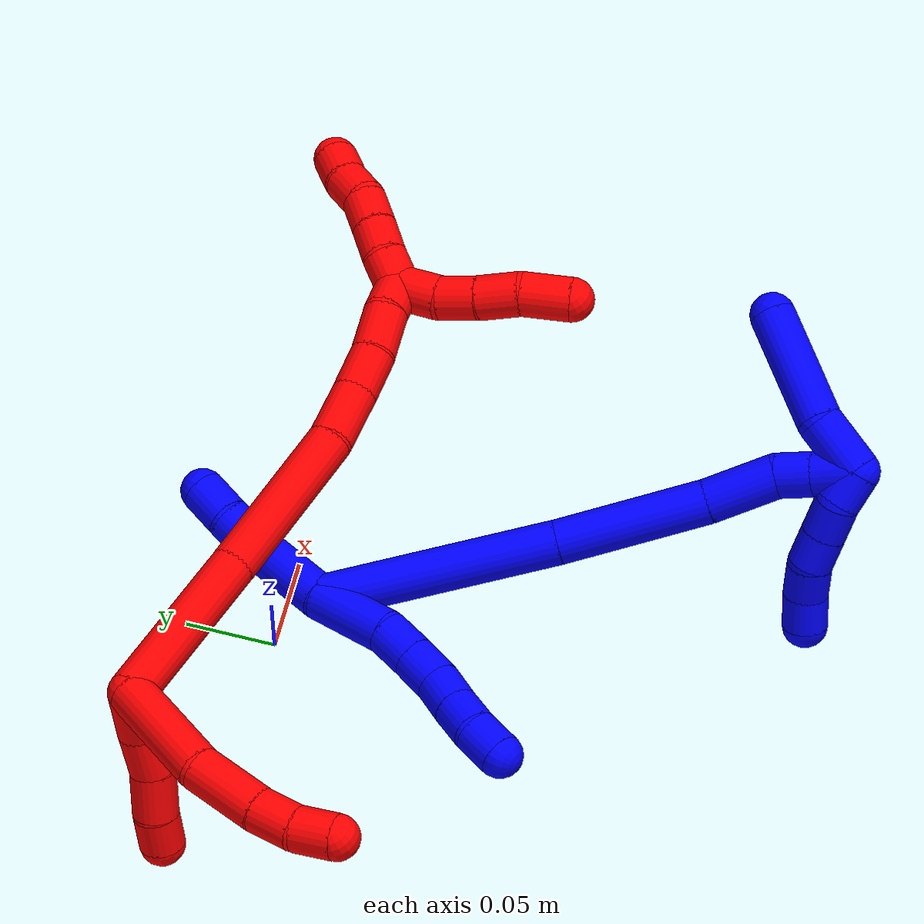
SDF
<sdf version="1.7">
 <world name="default">
  <plugin name="TubeGeneratorPlugin" filename="libtube_generator_plugin.so"/>
  <model name="photoneo_s_sensor">
   <static>1</static>
   <pose>0 0 2 1.57079 1.57079 3.14159</pose>
   <link name="link">
    <inertial><mass>0.1</mass></inertial>
    <sensor name="sensor" type="depth">
     <update_rate>30</update_rate>
     <camera>
      <horizontal_fov>1.22</horizontal_fov>
      <image><width>1920</width><height>1200</height><format>B8G8R8</format></image>
      <clip><near>0.1</near><far>4</far></clip>
      <depth_camera><output>points</output></depth_camera>
     </camera>
     <plugin name="camera_plugin" filename="libgazebo_ros_depth_camera.so">
      <baseline>0.2</baseline>
      <alwaysOn>1</alwaysOn>
      <updateRate>0.0</updateRate>
      <cameraName>camera_ir</cameraName>
      <imageTopicName>/camera/color/image_raw</imageTopicName>
      <cameraInfoTopicName>/camera/color/camera_info</cameraInfoTopicName>
      <depthImageTopicName>/camera/depth/image_raw</depthImageTopicName>
      <depthImageCameraInfoTopicName>/camera/depth/camera_info</depthImageCameraInfoTopicName>
      <pointCloudTopicName>/camera/depth/points</pointCloudTopicName>
      <frameName>fr_optical</frameName>
      <pointCloudCutoff>0.1</pointCloudCutoff>
      <pointCloudCutoffMax>2.0</pointCloudCutoffMax>
      <distortionK1>0</distortionK1>
      <distortionK2>0</distortionK2>
      <distortionK3>0</distortionK3>
      <distortionT1>0</distortionT1>
      <distortionT2>0</distortionT2>
      <CxPrime>0</CxPrime>
      <Cx>0</Cx>
      <Cy>0</Cy>
      <focalLength>0</focalLength>
      <hackBaseline>0</hackBaseline>
     </plugin>
    </sensor>
   </link>
  </model>
  <gravity>0 0 -9.8</gravity>
  <magnetic_field>6e-06 2.3e-05 -4.2e-05</magnetic_field>
  <atmosphere type="adiabatic"/>
  <physics name="default_physics" default="0" type="ode">
   <max_step_size>0.003</max_step_size>
   <real_time_factor>1</real_time_factor>
   <real_time_update_rate>1000</real_time_update_rate>
   <max_contacts>10000</max_contacts>
   <ode>
    <solver>
     <type>quick</type>
     <iters>100</iters>
     <sor>1.3</sor>
     <use_dynamic_moi_rescaling>0</use_dynamic_moi_rescaling>
    </solver>
    <constraints>
     <contact_max_correcting_vel>0</contact_max_correcting_vel>
     <contact_surface_layer>0.001</contact_surface_layer>
     <cfm>0</cfm>
     <erp>0.2</erp>
    </constraints>
   </ode>
  </physics>
  <scene><ambient>0.4 0.4 0.4 1</ambient><background>0.7 0.7 0.7 1</background><shadows>0</shadows></scene>
  <audio><device>default</device></audio>
  <spherical_coordinates>
   <surface_model>EARTH_WGS84</surface_model>
   <latitude_deg>0</latitude_deg>
   <longitude_deg>0</longitude_deg>
   <elevation>0</elevation>
   <heading_deg>0</heading_deg>
  </spherical_coordinates>
  <model name="bin">
   <static>1</static>
   <link name="bottom">
    <collision name="collision-bottom">
     <pose>0 0 -0.01 0 -0 0</pose>
     <geometry><box><size>0.8 0.6 0.02</size></box></geometry>
     <surface>
      <friction><ode><mu>100</mu><mu2>100</mu2></ode></friction>
      <contact><collide_bitmask>65535</collide_bitmask></contact>
     </surface>
    </collision>
   </link>
   <link name="west_wall">
    <collision name="collision-west_wall">
     <pose>-0.41 0 0.1 0 -0 0</pose>
     <geometry><box><size>0.02 0.6 0.2</size></box></geometry>
     <surface>
      <friction><ode><mu>100</mu><mu2>100</mu2></ode></friction>
      <contact><collide_bitmask>65535</collide_bitmask></contact>
     </surface>
    </collision>
   </link>
   <link name="east_wall">
    <collision name="collision-east_wall">
     <pose>0.41 0 0.1 0 -0 0</pose>
     <geometry><box><size>0.02 0.6 0.2</size></box></geometry>
     <surface>
      <friction><ode><mu>100</mu><mu2>100</mu2></ode></friction>
      <contact><collide_bitmask>65535</collide_bitmask></contact>
     </surface>
    </collision>
   </link>
   <link name="south_wall">
    <collision name="collision-south_wall">
     <pose>0 -0.31 0.1 0 -0 0</pose>
     <geometry><box><size>0.8 0.02 0.2</size></box></geometry>
     <surface>
      <friction><ode><mu>100</mu><mu2>100</mu2></ode></friction>
      <contact><collide_bitmask>65535</collide_bitmask></contact>
     </surface>
    </collision>
   </link>
   <link name="north_wall">
    <collision name="collision-north_wall">
     <pose>0 0.31 0.1 0 -0 0</pose>
     <geometry><box><size>0.8 0.02 0.2</size></box></geometry>
     <surface>
      <friction><ode><mu>100</mu><mu2>100</mu2></ode></friction>
      <contact><collide_bitmask>65535</collide_bitmask></contact>
     </surface>
    </collision>
   </link>
  </model>
  <model name="1">
   <static>0</static>
   <link name="1">
    <collision name="collision-cylinder-e_1_2_8">
     <pose>0.003318 -0.000159 0.022871 0.006957 0.144087 0.000502</pose>
     <geometry><cylinder><radius>0.0125</radius><length>0.046222</length></cylinder></geometry>
     <surface>
      <friction><ode><mu>1.16</mu><mu2>1.16</mu2><slip1>0</slip1><slip2>0</slip2></ode></friction>
      <contact><ode><kp>1e+06</kp><kd>1</kd><max_vel>0</max_vel><min_depth>0.001</min_depth></ode></contact>
     </surface>
    </collision>
    <visual name="visual-cylinder-e_1_2_8">
     <pose>0.003318 -0.000159 0.022871 0.006957 0.144087 0.000502</pose>
     <geometry><cylinder><radius>0.0125</radius><length>0.046222</length></cylinder></geometry>
     <material><ambient>0 0 1 1</ambient></material>
    </visual>
    <collision name="collision-cylinder-e_2_8_9">
     <pose>0.006511 0.001765 0.056602 -0.18955 -0.011362 0.00108</pose>
     <geometry><cylinder><radius>0.0125</radius><length>0.022118</length></cylinder></geometry>
     <surface>
      <friction><ode><mu>1.16</mu><mu2>1.16</mu2><slip1>0</slip1><slip2>0</slip2></ode></friction>
      <contact><ode><kp>1e+06</kp><kd>1</kd><max_vel>0</max_vel><min_depth>0.001</min_depth></ode></contact>
     </surface>
    </collision>
    <visual name="visual-cylinder-e_2_8_9">
     <pose>0.006511 0.001765 0.056602 -0.18955 -0.011362 0.00108</pose>
     <geometry><cylinder><radius>0.0125</radius><length>0.022118</length></cylinder></geometry>
     <material><ambient>0 0 1 1</ambient></material>
    </visual>
    <collision name="collision-cylinder-e_3_9_10">
     <pose>0.006359 0.006274 0.077666 -0.233363 -0.002557 0.0003</pose>
     <geometry><cylinder><radius>0.0125</radius><length>0.020976</length></cylinder></geometry>
     <surface>
      <friction><ode><mu>1.16</mu><mu2>1.16</mu2><slip1>0</slip1><slip2>0</slip2></ode></friction>
      <contact><ode><kp>1e+06</kp><kd>1</kd><max_vel>0</max_vel><min_depth>0.001</min_depth></ode></contact>
     </surface>
    </collision>
    <visual name="visual-cylinder-e_3_9_10">
     <pose>0.006359 0.006274 0.077666 -0.233363 -0.002557 0.0003</pose>
     <geometry><cylinder><radius>0.0125</radius><length>0.020976</length></cylinder></geometry>
     <material><ambient>0 0 1 1</ambient></material>
    </visual>
    <collision name="collision-cylinder-e_4_10_11">
     <pose>0.007836 0.012669 0.097094 -0.406338 0.148664 -0.030681</pose>
     <geometry><cylinder><radius>0.0125</radius><length>0.020308</length></cylinder></geometry>
     <surface>
      <friction><ode><mu>1.16</mu><mu2>1.16</mu2><slip1>0</slip1><slip2>0</slip2></ode></friction>
      <contact><ode><kp>1e+06</kp><kd>1</kd><max_vel>0</max_vel><min_depth>0.001</min_depth></ode></contact>
     </surface>
    </collision>
    <visual name="visual-cylinder-e_4_10_11">
     <pose>0.007836 0.012669 0.097094 -0.406338 0.148664 -0.030681</pose>
     <geometry><cylinder><radius>0.0125</radius><length>0.020308</length></cylinder></geometry>
     <material><ambient>0 0 1 1</ambient></material>
    </visual>
    <collision name="collision-cylinder-e_5_11_12">
     <pose>0.011058 0.020167 0.11552 -0.366214 0.172614 -0.032042</pose>
     <geometry><cylinder><radius>0.0125</radius><length>0.020009</length></cylinder></geometry>
     <surface>
      <friction><ode><mu>1.16</mu><mu2>1.16</mu2><slip1>0</slip1><slip2>0</slip2></ode></friction>
      <contact><ode><kp>1e+06</kp><kd>1</kd><max_vel>0</max_vel><min_depth>0.001</min_depth></ode></contact>
     </surface>
    </collision>
    <visual name="visual-cylinder-e_5_11_12">
     <pose>0.011058 0.020167 0.11552 -0.366214 0.172614 -0.032042</pose>
     <geometry><cylinder><radius>0.0125</radius><length>0.020009</length></cylinder></geometry>
     <material><ambient>0 0 1 1</ambient></material>
    </visual>
    <collision name="collision-cylinder-e_6_12_6">
     <pose>0.012884 0.025818 0.134682 -0.209886 0.010556 -0.001112</pose>
     <geometry><cylinder><radius>0.0125</radius><length>0.020367</length></cylinder></geometry>
     <surface>
      <friction><ode><mu>1.16</mu><mu2>1.16</mu2><slip1>0</slip1><slip2>0</slip2></ode></friction>
      <contact><ode><kp>1e+06</kp><kd>1</kd><max_vel>0</max_vel><min_depth>0.001</min_depth></ode></contact>
     </surface>
    </collision>
    <visual name="visual-cylinder-e_6_12_6">
     <pose>0.012884 0.025818 0.134682 -0.209886 0.010556 -0.001112</pose>
     <geometry><cylinder><radius>0.0125</radius><length>0.020367</length></cylinder></geometry>
     <material><ambient>0 0 1 1</ambient></material>
    </visual>
    <collision name="collision-cylinder-e_1_2_13">
     <pose>-0.003586 -0.004512 -0.026986 2.97593 -0.130334 -1.33238</pose>
     <geometry><cylinder><radius>0.0125</radius><length>0.055188</length></cylinder></geometry>
     <surface>
      <friction><ode><mu>1.16</mu><mu2>1.16</mu2><slip1>0</slip1><slip2>0</slip2></ode></friction>
      <contact><ode><kp>1e+06</kp><kd>1</kd><max_vel>0</max_vel><min_depth>0.001</min_depth></ode></contact>
     </surface>
    </collision>
    <visual name="visual-cylinder-e_1_2_13">
     <pose>-0.003586 -0.004512 -0.026986 2.97593 -0.130334 -1.33238</pose>
     <geometry><cylinder><radius>0.0125</radius><length>0.055188</length></cylinder></geometry>
     <material><ambient>0 0 1 1</ambient></material>
    </visual>
    <collision name="collision-cylinder-e_2_13_14">
     <pose>-0.004801 -0.010677 -0.064565 2.98676 0.217713 1.90704</pose>
     <geometry><cylinder><radius>0.0125</radius><length>0.021963</length></cylinder></geometry>
     <surface>
      <friction><ode><mu>1.16</mu><mu2>1.16</mu2><slip1>0</slip1><slip2>0</slip2></ode></friction>
      <contact><ode><kp>1e+06</kp><kd>1</kd><max_vel>0</max_vel><min_depth>0.001</min_depth></ode></contact>
     </surface>
    </collision>
    <visual name="visual-cylinder-e_2_13_14">
     <pose>-0.004801 -0.010677 -0.064565 2.98676 0.217713 1.90704</pose>
     <geometry><cylinder><radius>0.0125</radius><length>0.021963</length></cylinder></geometry>
     <material><ambient>0 0 1 1</ambient></material>
    </visual>
    <collision name="collision-cylinder-e_3_14_5">
     <pose>-0.001889 -0.015088 -0.086233 2.89759 0.047296 0.381138</pose>
     <geometry><cylinder><radius>0.0125</radius><length>0.022849</length></cylinder></geometry>
     <surface>
      <friction><ode><mu>1.16</mu><mu2>1.16</mu2><slip1>0</slip1><slip2>0</slip2></ode></friction>
      <contact><ode><kp>1e+06</kp><kd>1</kd><max_vel>0</max_vel><min_depth>0.001</min_depth></ode></contact>
     </surface>
    </collision>
    <visual name="visual-cylinder-e_3_14_5">
     <pose>-0.001889 -0.015088 -0.086233 2.89759 0.047296 0.381138</pose>
     <geometry><cylinder><radius>0.0125</radius><length>0.022849</length></cylinder></geometry>
     <material><ambient>0 0 1 1</ambient></material>
    </visual>
    <collision name="collision-cylinder-e_1_2_15">
     <pose>0.007583 -0.047248 0.045644 0.802663 0.114919 0.048812</pose>
     <geometry><cylinder><radius>0.0125</radius><length>0.132262</length></cylinder></geometry>
     <surface>
      <friction><ode><mu>1.16</mu><mu2>1.16</mu2><slip1>0</slip1><slip2>0</slip2></ode></friction>
      <contact><ode><kp>1e+06</kp><kd>1</kd><max_vel>0</max_vel><min_depth>0.001</min_depth></ode></contact>
     </surface>
    </collision>
    <visual name="visual-cylinder-e_1_2_15">
     <pose>0.007583 -0.047248 0.045644 0.802663 0.114919 0.048812</pose>
     <geometry><cylinder><radius>0.0125</radius><length>0.132262</length></cylinder></geometry>
     <material><ambient>0 0 1 1</ambient></material>
    </visual>
    <collision name="collision-cylinder-e_2_15_16">
     <pose>0.020786 -0.125207 0.119176 0.833539 0.13466 0.059687</pose>
     <geometry><cylinder><radius>0.0125</radius><length>0.083724</length></cylinder></geometry>
     <surface>
      <friction><ode><mu>1.16</mu><mu2>1.16</mu2><slip1>0</slip1><slip2>0</slip2></ode></friction>
      <contact><ode><kp>1e+06</kp><kd>1</kd><max_vel>0</max_vel><min_depth>0.001</min_depth></ode></contact>
     </surface>
    </collision>
    <visual name="visual-cylinder-e_2_15_16">
     <pose>0.020786 -0.125207 0.119176 0.833539 0.13466 0.059687</pose>
     <geometry><cylinder><radius>0.0125</radius><length>0.083724</length></cylinder></geometry>
     <material><ambient>0 0 1 1</ambient></material>
    </visual>
    <collision name="collision-cylinder-e_3_16_17">
     <pose>0.031072 -0.170757 0.159477 0.874166 0.236663 0.110979</pose>
     <geometry><cylinder><radius>0.0125</radius><length>0.039805</length></cylinder></geometry>
     <surface>
      <friction><ode><mu>1.16</mu><mu2>1.16</mu2><slip1>0</slip1><slip2>0</slip2></ode></friction>
      <contact><ode><kp>1e+06</kp><kd>1</kd><max_vel>0</max_vel><min_depth>0.001</min_depth></ode></contact>
     </surface>
    </collision>
    <visual name="visual-cylinder-e_3_16_17">
     <pose>0.031072 -0.170757 0.159477 0.874166 0.236663 0.110979</pose>
     <geometry><cylinder><radius>0.0125</radius><length>0.039805</length></cylinder></geometry>
     <material><ambient>0 0 1 1</ambient></material>
    </visual>
    <collision name="collision-cylinder-e_4_17_18">
     <pose>0.037405 -0.190741 0.180443 0.541528 0.165439 0.04602</pose>
     <geometry><cylinder><radius>0.0125</radius><length>0.020234</length></cylinder></geometry>
     <surface>
      <friction><ode><mu>1.16</mu><mu2>1.16</mu2><slip1>0</slip1><slip2>0</slip2></ode></friction>
      <contact><ode><kp>1e+06</kp><kd>1</kd><max_vel>0</max_vel><min_depth>0.001</min_depth></ode></contact>
     </surface>
    </collision>
    <visual name="visual-cylinder-e_4_17_18">
     <pose>0.037405 -0.190741 0.180443 0.541528 0.165439 0.04602</pose>
     <geometry><cylinder><radius>0.0125</radius><length>0.020234</length></cylinder></geometry>
     <material><ambient>0 0 1 1</ambient></material>
    </visual>
    <collision name="collision-cylinder-e_5_18_1">
     <pose>0.041636 -0.201863 0.199063 0.535823 0.215658 0.059414</pose>
     <geometry><cylinder><radius>0.0125</radius><length>0.023975</length></cylinder></geometry>
     <surface>
      <friction><ode><mu>1.16</mu><mu2>1.16</mu2><slip1>0</slip1><slip2>0</slip2></ode></friction>
      <contact><ode><kp>1e+06</kp><kd>1</kd><max_vel>0</max_vel><min_depth>0.001</min_depth></ode></contact>
     </surface>
    </collision>
    <visual name="visual-cylinder-e_5_18_1">
     <pose>0.041636 -0.201863 0.199063 0.535823 0.215658 0.059414</pose>
     <geometry><cylinder><radius>0.0125</radius><length>0.023975</length></cylinder></geometry>
     <material><ambient>0 0 1 1</ambient></material>
    </visual>
    <collision name="collision-cylinder-e_1_1_19">
     <pose>0.038485 -0.199686 0.208225 -1.68151 -0.608474 0.674819</pose>
     <geometry><cylinder><radius>0.0125</radius><length>0.02</length></cylinder></geometry>
     <surface>
      <friction><ode><mu>1.16</mu><mu2>1.16</mu2><slip1>0</slip1><slip2>0</slip2></ode></friction>
      <contact><ode><kp>1e+06</kp><kd>1</kd><max_vel>0</max_vel><min_depth>0.001</min_depth></ode></contact>
     </surface>
    </collision>
    <visual name="visual-cylinder-e_1_1_19">
     <pose>0.038485 -0.199686 0.208225 -1.68151 -0.608474 0.674819</pose>
     <geometry><cylinder><radius>0.0125</radius><length>0.02</length></cylinder></geometry>
     <material><ambient>0 0 1 1</ambient></material>
    </visual>
    <collision name="collision-cylinder-e_2_19_20">
     <pose>0.024642 -0.185734 0.206731 -1.67175 -0.948803 1.03336</pose>
     <geometry><cylinder><radius>0.0125</radius><length>0.02</length></cylinder></geometry>
     <surface>
      <friction><ode><mu>1.16</mu><mu2>1.16</mu2><slip1>0</slip1><slip2>0</slip2></ode></friction>
      <contact><ode><kp>1e+06</kp><kd>1</kd><max_vel>0</max_vel><min_depth>0.001</min_depth></ode></contact>
     </surface>
    </collision>
    <visual name="visual-cylinder-e_2_19_20">
     <pose>0.024642 -0.185734 0.206731 -1.67175 -0.948803 1.03336</pose>
     <geometry><cylinder><radius>0.0125</radius><length>0.02</length></cylinder></geometry>
     <material><ambient>0 0 1 1</ambient></material>
    </visual>
    <collision name="collision-cylinder-e_3_20_21">
     <pose>0.008513 -0.17396 0.205648 -1.6536 -0.927542 0.995497</pose>
     <geometry><cylinder><radius>0.0125</radius><length>0.02</length></cylinder></geometry>
     <surface>
      <friction><ode><mu>1.16</mu><mu2>1.16</mu2><slip1>0</slip1><slip2>0</slip2></ode></friction>
      <contact><ode><kp>1e+06</kp><kd>1</kd><max_vel>0</max_vel><min_depth>0.001</min_depth></ode></contact>
     </surface>
    </collision>
    <visual name="visual-cylinder-e_3_20_21">
     <pose>0.008513 -0.17396 0.205648 -1.6536 -0.927542 0.995497</pose>
     <geometry><cylinder><radius>0.0125</radius><length>0.02</length></cylinder></geometry>
     <material><ambient>0 0 1 1</ambient></material>
    </visual>
    <collision name="collision-cylinder-e_4_21_22">
     <pose>-0.008696 -0.164221 0.206185 -1.30273 -1.17004 0.935225</pose>
     <geometry><cylinder><radius>0.0125</radius><length>0.02</length></cylinder></geometry>
     <surface>
      <friction><ode><mu>1.16</mu><mu2>1.16</mu2><slip1>0</slip1><slip2>0</slip2></ode></friction>
      <contact><ode><kp>1e+06</kp><kd>1</kd><max_vel>0</max_vel><min_depth>0.001</min_depth></ode></contact>
     </surface>
    </collision>
    <visual name="visual-cylinder-e_4_21_22">
     <pose>-0.008696 -0.164221 0.206185 -1.30273 -1.17004 0.935225</pose>
     <geometry><cylinder><radius>0.0125</radius><length>0.02</length></cylinder></geometry>
     <material><ambient>0 0 1 1</ambient></material>
    </visual>
    <collision name="collision-cylinder-e_5_22_4">
     <pose>-0.026583 -0.156194 0.209763 -1.03287 -1.05111 0.636276</pose>
     <geometry><cylinder><radius>0.0125</radius><length>0.02</length></cylinder></geometry>
     <surface>
      <friction><ode><mu>1.16</mu><mu2>1.16</mu2><slip1>0</slip1><slip2>0</slip2></ode></friction>
      <contact><ode><kp>1e+06</kp><kd>1</kd><max_vel>0</max_vel><min_depth>0.001</min_depth></ode></contact>
     </surface>
    </collision>
    <visual name="visual-cylinder-e_5_22_4">
     <pose>-0.026583 -0.156194 0.209763 -1.03287 -1.05111 0.636276</pose>
     <geometry><cylinder><radius>0.0125</radius><length>0.02</length></cylinder></geometry>
     <material><ambient>0 0 1 1</ambient></material>
    </visual>
    <collision name="collision-cylinder-e_1_1_23">
     <pose>0.050447 -0.211894 0.19406 2.87892 0.380685 1.93962</pose>
     <geometry><cylinder><radius>0.0125</radius><length>0.03362</length></cylinder></geometry>
     <surface>
      <friction><ode><mu>1.16</mu><mu2>1.16</mu2><slip1>0</slip1><slip2>0</slip2></ode></friction>
      <contact><ode><kp>1e+06</kp><kd>1</kd><max_vel>0</max_vel><min_depth>0.001</min_depth></ode></contact>
     </surface>
    </collision>
    <visual name="visual-cylinder-e_1_1_23">
     <pose>0.050447 -0.211894 0.19406 2.87892 0.380685 1.93962</pose>
     <geometry><cylinder><radius>0.0125</radius><length>0.03362</length></cylinder></geometry>
     <material><ambient>0 0 1 1</ambient></material>
    </visual>
    <collision name="collision-cylinder-e_2_23_3">
     <pose>0.06401 -0.233092 0.151529 2.58345 0.22227 0.74274</pose>
     <geometry><cylinder><radius>0.0125</radius><length>0.06638</length></cylinder></geometry>
     <surface>
      <friction><ode><mu>1.16</mu><mu2>1.16</mu2><slip1>0</slip1><slip2>0</slip2></ode></friction>
      <contact><ode><kp>1e+06</kp><kd>1</kd><max_vel>0</max_vel><min_depth>0.001</min_depth></ode></contact>
     </surface>
    </collision>
    <visual name="visual-cylinder-e_2_23_3">
     <pose>0.06401 -0.233092 0.151529 2.58345 0.22227 0.74274</pose>
     <geometry><cylinder><radius>0.0125</radius><length>0.06638</length></cylinder></geometry>
     <material><ambient>0 0 1 1</ambient></material>
    </visual>
    <collision name="collision-sphere-3">
     <pose>0.071326 -0.250237 0.124068 0 -0 0</pose>
     <geometry><sphere><radius>0.0125</radius></sphere></geometry>
     <surface>
      <friction><ode><mu>1.16</mu><mu2>1.16</mu2><slip1>0</slip1><slip2>0</slip2></ode></friction>
      <contact><ode><kp>1e+06</kp><kd>1</kd><max_vel>0</max_vel><min_depth>0.001</min_depth></ode></contact>
     </surface>
    </collision>
    <visual name="visual-sphere-3">
     <pose>0.071326 -0.250237 0.124068 0 -0 0</pose>
     <geometry><sphere><radius>0.0125</radius></sphere></geometry>
     <material><ambient>0 0 1 1</ambient></material>
    </visual>
    <collision name="collision-sphere-23">
     <pose>0.056693 -0.215946 0.178989 0 -0 0</pose>
     <geometry><sphere><radius>0.0125</radius></sphere></geometry>
     <surface>
      <friction><ode><mu>1.16</mu><mu2>1.16</mu2><slip1>0</slip1><slip2>0</slip2></ode></friction>
      <contact><ode><kp>1e+06</kp><kd>1</kd><max_vel>0</max_vel><min_depth>0.001</min_depth></ode></contact>
     </surface>
    </collision>
    <visual name="visual-sphere-23">
     <pose>0.056693 -0.215946 0.178989 0 -0 0</pose>
     <geometry><sphere><radius>0.0125</radius></sphere></geometry>
     <material><ambient>0 0 1 1</ambient></material>
    </visual>
    <collision name="collision-sphere-4">
     <pose>-0.035263 -0.15193 0.212307 0 -0 0</pose>
     <geometry><sphere><radius>0.0125</radius></sphere></geometry>
     <surface>
      <friction><ode><mu>1.16</mu><mu2>1.16</mu2><slip1>0</slip1><slip2>0</slip2></ode></friction>
      <contact><ode><kp>1e+06</kp><kd>1</kd><max_vel>0</max_vel><min_depth>0.001</min_depth></ode></contact>
     </surface>
    </collision>
    <visual name="visual-sphere-4">
     <pose>-0.035263 -0.15193 0.212307 0 -0 0</pose>
     <geometry><sphere><radius>0.0125</radius></sphere></geometry>
     <material><ambient>0 0 1 1</ambient></material>
    </visual>
    <collision name="collision-sphere-22">
     <pose>-0.017903 -0.160459 0.207218 0 -0 0</pose>
     <geometry><sphere><radius>0.0125</radius></sphere></geometry>
     <surface>
      <friction><ode><mu>1.16</mu><mu2>1.16</mu2><slip1>0</slip1><slip2>0</slip2></ode></friction>
      <contact><ode><kp>1e+06</kp><kd>1</kd><max_vel>0</max_vel><min_depth>0.001</min_depth></ode></contact>
     </surface>
    </collision>
    <visual name="visual-sphere-22">
     <pose>-0.017903 -0.160459 0.207218 0 -0 0</pose>
     <geometry><sphere><radius>0.0125</radius></sphere></geometry>
     <material><ambient>0 0 1 1</ambient></material>
    </visual>
    <collision name="collision-sphere-21">
     <pose>0.000512 -0.167983 0.205152 0 -0 0</pose>
     <geometry><sphere><radius>0.0125</radius></sphere></geometry>
     <surface>
      <friction><ode><mu>1.16</mu><mu2>1.16</mu2><slip1>0</slip1><slip2>0</slip2></ode></friction>
      <contact><ode><kp>1e+06</kp><kd>1</kd><max_vel>0</max_vel><min_depth>0.001</min_depth></ode></contact>
     </surface>
    </collision>
    <visual name="visual-sphere-21">
     <pose>0.000512 -0.167983 0.205152 0 -0 0</pose>
     <geometry><sphere><radius>0.0125</radius></sphere></geometry>
     <material><ambient>0 0 1 1</ambient></material>
    </visual>
    <collision name="collision-sphere-20">
     <pose>0.016515 -0.179938 0.206144 0 -0 0</pose>
     <geometry><sphere><radius>0.0125</radius></sphere></geometry>
     <surface>
      <friction><ode><mu>1.16</mu><mu2>1.16</mu2><slip1>0</slip1><slip2>0</slip2></ode></friction>
      <contact><ode><kp>1e+06</kp><kd>1</kd><max_vel>0</max_vel><min_depth>0.001</min_depth></ode></contact>
     </surface>
    </collision>
    <visual name="visual-sphere-20">
     <pose>0.016515 -0.179938 0.206144 0 -0 0</pose>
     <geometry><sphere><radius>0.0125</radius></sphere></geometry>
     <material><ambient>0 0 1 1</ambient></material>
    </visual>
    <collision name="collision-sphere-12">
     <pose>0.012777 0.023696 0.124723 0 -0 0</pose>
     <geometry><sphere><radius>0.0125</radius></sphere></geometry>
     <surface>
      <friction><ode><mu>1.16</mu><mu2>1.16</mu2><slip1>0</slip1><slip2>0</slip2></ode></friction>
      <contact><ode><kp>1e+06</kp><kd>1</kd><max_vel>0</max_vel><min_depth>0.001</min_depth></ode></contact>
     </surface>
    </collision>
    <visual name="visual-sphere-12">
     <pose>0.012777 0.023696 0.124723 0 -0 0</pose>
     <geometry><sphere><radius>0.0125</radius></sphere></geometry>
     <material><ambient>0 0 1 1</ambient></material>
    </visual>
    <collision name="collision-sphere-11">
     <pose>0.00934 0.016638 0.106318 0 -0 0</pose>
     <geometry><sphere><radius>0.0125</radius></sphere></geometry>
     <surface>
      <friction><ode><mu>1.16</mu><mu2>1.16</mu2><slip1>0</slip1><slip2>0</slip2></ode></friction>
      <contact><ode><kp>1e+06</kp><kd>1</kd><max_vel>0</max_vel><min_depth>0.001</min_depth></ode></contact>
     </surface>
    </collision>
    <visual name="visual-sphere-11">
     <pose>0.00934 0.016638 0.106318 0 -0 0</pose>
     <geometry><sphere><radius>0.0125</radius></sphere></geometry>
     <material><ambient>0 0 1 1</ambient></material>
    </visual>
    <collision name="collision-sphere-10">
     <pose>0.006332 0.0087 0.08787 0 -0 0</pose>
     <geometry><sphere><radius>0.0125</radius></sphere></geometry>
     <surface>
      <friction><ode><mu>1.16</mu><mu2>1.16</mu2><slip1>0</slip1><slip2>0</slip2></ode></friction>
      <contact><ode><kp>1e+06</kp><kd>1</kd><max_vel>0</max_vel><min_depth>0.001</min_depth></ode></contact>
     </surface>
    </collision>
    <visual name="visual-sphere-10">
     <pose>0.006332 0.0087 0.08787 0 -0 0</pose>
     <geometry><sphere><radius>0.0125</radius></sphere></geometry>
     <material><ambient>0 0 1 1</ambient></material>
    </visual>
    <collision name="collision-sphere-9">
     <pose>0.006386 0.003849 0.067463 0 -0 0</pose>
     <geometry><sphere><radius>0.0125</radius></sphere></geometry>
     <surface>
      <friction><ode><mu>1.16</mu><mu2>1.16</mu2><slip1>0</slip1><slip2>0</slip2></ode></friction>
      <contact><ode><kp>1e+06</kp><kd>1</kd><max_vel>0</max_vel><min_depth>0.001</min_depth></ode></contact>
     </surface>
    </collision>
    <visual name="visual-sphere-9">
     <pose>0.006386 0.003849 0.067463 0 -0 0</pose>
     <geometry><sphere><radius>0.0125</radius></sphere></geometry>
     <material><ambient>0 0 1 1</ambient></material>
    </visual>
    <collision name="collision-sphere-2">
     <geometry><sphere><radius>0.0125</radius></sphere></geometry>
     <surface>
      <friction><ode><mu>1.16</mu><mu2>1.16</mu2><slip1>0</slip1><slip2>0</slip2></ode></friction>
      <contact><ode><kp>1e+06</kp><kd>1</kd><max_vel>0</max_vel><min_depth>0.001</min_depth></ode></contact>
     </surface>
    </collision>
    <visual name="visual-sphere-2">
     <geometry><sphere><radius>0.0125</radius></sphere></geometry>
     <material><ambient>0 0 1 1</ambient></material>
    </visual>
    <collision name="collision-sphere-19">
     <pose>0.032769 -0.191531 0.207318 0 -0 0</pose>
     <geometry><sphere><radius>0.0125</radius></sphere></geometry>
     <surface>
      <friction><ode><mu>1.16</mu><mu2>1.16</mu2><slip1>0</slip1><slip2>0</slip2></ode></friction>
      <contact><ode><kp>1e+06</kp><kd>1</kd><max_vel>0</max_vel><min_depth>0.001</min_depth></ode></contact>
     </surface>
    </collision>
    <visual name="visual-sphere-19">
     <pose>0.032769 -0.191531 0.207318 0 -0 0</pose>
     <geometry><sphere><radius>0.0125</radius></sphere></geometry>
     <material><ambient>0 0 1 1</ambient></material>
    </visual>
    <collision name="collision-sphere-8">
     <pose>0.006637 -0.000318 0.045742 0 -0 0</pose>
     <geometry><sphere><radius>0.0125</radius></sphere></geometry>
     <surface>
      <friction><ode><mu>1.16</mu><mu2>1.16</mu2><slip1>0</slip1><slip2>0</slip2></ode></friction>
      <contact><ode><kp>1e+06</kp><kd>1</kd><max_vel>0</max_vel><min_depth>0.001</min_depth></ode></contact>
     </surface>
    </collision>
    <visual name="visual-sphere-8">
     <pose>0.006637 -0.000318 0.045742 0 -0 0</pose>
     <geometry><sphere><radius>0.0125</radius></sphere></geometry>
     <material><ambient>0 0 1 1</ambient></material>
    </visual>
    <collision name="collision-sphere-6">
     <pose>0.012992 0.027939 0.144642 0 -0 0</pose>
     <geometry><sphere><radius>0.0125</radius></sphere></geometry>
     <surface>
      <friction><ode><mu>1.16</mu><mu2>1.16</mu2><slip1>0</slip1><slip2>0</slip2></ode></friction>
      <contact><ode><kp>1e+06</kp><kd>1</kd><max_vel>0</max_vel><min_depth>0.001</min_depth></ode></contact>
     </surface>
    </collision>
    <visual name="visual-sphere-6">
     <pose>0.012992 0.027939 0.144642 0 -0 0</pose>
     <geometry><sphere><radius>0.0125</radius></sphere></geometry>
     <material><ambient>0 0 1 1</ambient></material>
    </visual>
    <collision name="collision-sphere-13">
     <pose>-0.007173 -0.009024 -0.053971 0 -0 0</pose>
     <geometry><sphere><radius>0.0125</radius></sphere></geometry>
     <surface>
      <friction><ode><mu>1.16</mu><mu2>1.16</mu2><slip1>0</slip1><slip2>0</slip2></ode></friction>
      <contact><ode><kp>1e+06</kp><kd>1</kd><max_vel>0</max_vel><min_depth>0.001</min_depth></ode></contact>
     </surface>
    </collision>
    <visual name="visual-sphere-13">
     <pose>-0.007173 -0.009024 -0.053971 0 -0 0</pose>
     <geometry><sphere><radius>0.0125</radius></sphere></geometry>
     <material><ambient>0 0 1 1</ambient></material>
    </visual>
    <collision name="collision-sphere-14">
     <pose>-0.002429 -0.012331 -0.075159 0 -0 0</pose>
     <geometry><sphere><radius>0.0125</radius></sphere></geometry>
     <surface>
      <friction><ode><mu>1.16</mu><mu2>1.16</mu2><slip1>0</slip1><slip2>0</slip2></ode></friction>
      <contact><ode><kp>1e+06</kp><kd>1</kd><max_vel>0</max_vel><min_depth>0.001</min_depth></ode></contact>
     </surface>
    </collision>
    <visual name="visual-sphere-14">
     <pose>-0.002429 -0.012331 -0.075159 0 -0 0</pose>
     <geometry><sphere><radius>0.0125</radius></sphere></geometry>
     <material><ambient>0 0 1 1</ambient></material>
    </visual>
    <collision name="collision-sphere-5">
     <pose>-0.001348 -0.017844 -0.097306 0 -0 0</pose>
     <geometry><sphere><radius>0.0125</radius></sphere></geometry>
     <surface>
      <friction><ode><mu>1.16</mu><mu2>1.16</mu2><slip1>0</slip1><slip2>0</slip2></ode></friction>
      <contact><ode><kp>1e+06</kp><kd>1</kd><max_vel>0</max_vel><min_depth>0.001</min_depth></ode></contact>
     </surface>
    </collision>
    <visual name="visual-sphere-5">
     <pose>-0.001348 -0.017844 -0.097306 0 -0 0</pose>
     <geometry><sphere><radius>0.0125</radius></sphere></geometry>
     <material><ambient>0 0 1 1</ambient></material>
    </visual>
    <collision name="collision-sphere-15">
     <pose>0.015166 -0.094496 0.091288 0 -0 0</pose>
     <geometry><sphere><radius>0.0125</radius></sphere></geometry>
     <surface>
      <friction><ode><mu>1.16</mu><mu2>1.16</mu2><slip1>0</slip1><slip2>0</slip2></ode></friction>
      <contact><ode><kp>1e+06</kp><kd>1</kd><max_vel>0</max_vel><min_depth>0.001</min_depth></ode></contact>
     </surface>
    </collision>
    <visual name="visual-sphere-15">
     <pose>0.015166 -0.094496 0.091288 0 -0 0</pose>
     <geometry><sphere><radius>0.0125</radius></sphere></geometry>
     <material><ambient>0 0 1 1</ambient></material>
    </visual>
    <collision name="collision-sphere-16">
     <pose>0.026406 -0.155917 0.147063 0 -0 0</pose>
     <geometry><sphere><radius>0.0125</radius></sphere></geometry>
     <surface>
      <friction><ode><mu>1.16</mu><mu2>1.16</mu2><slip1>0</slip1><slip2>0</slip2></ode></friction>
      <contact><ode><kp>1e+06</kp><kd>1</kd><max_vel>0</max_vel><min_depth>0.001</min_depth></ode></contact>
     </surface>
    </collision>
    <visual name="visual-sphere-16">
     <pose>0.026406 -0.155917 0.147063 0 -0 0</pose>
     <geometry><sphere><radius>0.0125</radius></sphere></geometry>
     <material><ambient>0 0 1 1</ambient></material>
    </visual>
    <collision name="collision-sphere-17">
     <pose>0.035739 -0.185597 0.171892 0 -0 0</pose>
     <geometry><sphere><radius>0.0125</radius></sphere></geometry>
     <surface>
      <friction><ode><mu>1.16</mu><mu2>1.16</mu2><slip1>0</slip1><slip2>0</slip2></ode></friction>
      <contact><ode><kp>1e+06</kp><kd>1</kd><max_vel>0</max_vel><min_depth>0.001</min_depth></ode></contact>
     </surface>
    </collision>
    <visual name="visual-sphere-17">
     <pose>0.035739 -0.185597 0.171892 0 -0 0</pose>
     <geometry><sphere><radius>0.0125</radius></sphere></geometry>
     <material><ambient>0 0 1 1</ambient></material>
    </visual>
    <collision name="collision-sphere-18">
     <pose>0.039071 -0.195884 0.188994 0 -0 0</pose>
     <geometry><sphere><radius>0.0125</radius></sphere></geometry>
     <surface>
      <friction><ode><mu>1.16</mu><mu2>1.16</mu2><slip1>0</slip1><slip2>0</slip2></ode></friction>
      <contact><ode><kp>1e+06</kp><kd>1</kd><max_vel>0</max_vel><min_depth>0.001</min_depth></ode></contact>
     </surface>
    </collision>
    <visual name="visual-sphere-18">
     <pose>0.039071 -0.195884 0.188994 0 -0 0</pose>
     <geometry><sphere><radius>0.0125</radius></sphere></geometry>
     <material><ambient>0 0 1 1</ambient></material>
    </visual>
    <collision name="collision-sphere-1">
     <pose>0.044202 -0.207841 0.209131 0 -0 0</pose>
     <geometry><sphere><radius>0.0125</radius></sphere></geometry>
     <surface>
      <friction><ode><mu>1.16</mu><mu2>1.16</mu2><slip1>0</slip1><slip2>0</slip2></ode></friction>
      <contact><ode><kp>1e+06</kp><kd>1</kd><max_vel>0</max_vel><min_depth>0.001</min_depth></ode></contact>
     </surface>
    </collision>
    <visual name="visual-sphere-1">
     <pose>0.044202 -0.207841 0.209131 0 -0 0</pose>
     <geometry><sphere><radius>0.0125</radius></sphere></geometry>
     <material><ambient>0 0 1 1</ambient></material>
    </visual>
    <inertial>
     <pose>0.017513 -0.095865 0.098916 0 -0 0</pose>
     <mass>0.75</mass>
     <inertia>
      <ixx>0.000327</ixx>
      <ixy>0</ixy>
      <ixz>0</ixz>
      <iyy>0.000197</iyy>
      <iyz>0</iyz>
      <izz>0.000178</izz>
     </inertia>
    </inertial>
   </link>
   <pose>0.021729 -0.020742 0.026726 0.354231 -1.43575 0.824042</pose>
  </model>
  <model name="2">
   <static>0</static>
   <link name="2">
    <collision name="collision-cylinder-e_1_2_8">
     <pose>-0.01746 -0.025716 -0.006687 1.82521 -0.581367 -0.738332</pose>
     <geometry><cylinder><radius>0.0125</radius><length>0.063589</length></cylinder></geometry>
     <surface>
      <friction><ode><mu>1.16</mu><mu2>1.16</mu2><slip1>0</slip1><slip2>0</slip2></ode></friction>
      <contact><ode><kp>1e+06</kp><kd>1</kd><max_vel>0</max_vel><min_depth>0.001</min_depth></ode></contact>
     </surface>
    </collision>
    <visual name="visual-cylinder-e_1_2_8">
     <pose>-0.01746 -0.025716 -0.006687 1.82521 -0.581367 -0.738332</pose>
     <geometry><cylinder><radius>0.0125</radius><length>0.063589</length></cylinder></geometry>
     <material><ambient>1 0 0 1</ambient></material>
    </visual>
    <collision name="collision-cylinder-e_2_8_9">
     <pose>-0.041715 -0.069222 -0.020168 1.93554 -0.342669 -0.492371</pose>
     <geometry><cylinder><radius>0.0125</radius><length>0.040439</length></cylinder></geometry>
     <surface>
      <friction><ode><mu>1.16</mu><mu2>1.16</mu2><slip1>0</slip1><slip2>0</slip2></ode></friction>
      <contact><ode><kp>1e+06</kp><kd>1</kd><max_vel>0</max_vel><min_depth>0.001</min_depth></ode></contact>
     </surface>
    </collision>
    <visual name="visual-cylinder-e_2_8_9">
     <pose>-0.041715 -0.069222 -0.020168 1.93554 -0.342669 -0.492371</pose>
     <geometry><cylinder><radius>0.0125</radius><length>0.040439</length></cylinder></geometry>
     <material><ambient>1 0 0 1</ambient></material>
    </visual>
    <collision name="collision-cylinder-e_3_9_10">
     <pose>-0.05115 -0.097956 -0.030251 1.86288 -0.227145 -0.304439</pose>
     <geometry><cylinder><radius>0.0125</radius><length>0.023456</length></cylinder></geometry>
     <surface>
      <friction><ode><mu>1.16</mu><mu2>1.16</mu2><slip1>0</slip1><slip2>0</slip2></ode></friction>
      <contact><ode><kp>1e+06</kp><kd>1</kd><max_vel>0</max_vel><min_depth>0.001</min_depth></ode></contact>
     </surface>
    </collision>
    <visual name="visual-cylinder-e_3_9_10">
     <pose>-0.05115 -0.097956 -0.030251 1.86288 -0.227145 -0.304439</pose>
     <geometry><cylinder><radius>0.0125</radius><length>0.023456</length></cylinder></geometry>
     <material><ambient>1 0 0 1</ambient></material>
    </visual>
    <collision name="collision-cylinder-e_4_10_6">
     <pose>-0.053759 -0.119876 -0.036045 1.79503 0.002817 0.003532</pose>
     <geometry><cylinder><radius>0.0125</radius><length>0.022516</length></cylinder></geometry>
     <surface>
      <friction><ode><mu>1.16</mu><mu2>1.16</mu2><slip1>0</slip1><slip2>0</slip2></ode></friction>
      <contact><ode><kp>1e+06</kp><kd>1</kd><max_vel>0</max_vel><min_depth>0.001</min_depth></ode></contact>
     </surface>
    </collision>
    <visual name="visual-cylinder-e_4_10_6">
     <pose>-0.053759 -0.119876 -0.036045 1.79503 0.002817 0.003532</pose>
     <geometry><cylinder><radius>0.0125</radius><length>0.022516</length></cylinder></geometry>
     <material><ambient>1 0 0 1</ambient></material>
    </visual>
    <collision name="collision-cylinder-e_1_2_11">
     <pose>-0.002865 0.002372 -0.013254 -2.96448 -0.209653 1.7397</pose>
     <geometry><cylinder><radius>0.0125</radius><length>0.027533</length></cylinder></geometry>
     <surface>
      <friction><ode><mu>1.16</mu><mu2>1.16</mu2><slip1>0</slip1><slip2>0</slip2></ode></friction>
      <contact><ode><kp>1e+06</kp><kd>1</kd><max_vel>0</max_vel><min_depth>0.001</min_depth></ode></contact>
     </surface>
    </collision>
    <visual name="visual-cylinder-e_1_2_11">
     <pose>-0.002865 0.002372 -0.013254 -2.96448 -0.209653 1.7397</pose>
     <geometry><cylinder><radius>0.0125</radius><length>0.027533</length></cylinder></geometry>
     <material><ambient>1 0 0 1</ambient></material>
    </visual>
    <collision name="collision-cylinder-e_2_11_12">
     <pose>-0.009584 0.005196 -0.038373 -3.10361 -0.313864 2.90269</pose>
     <geometry><cylinder><radius>0.0125</radius><length>0.024965</length></cylinder></geometry>
     <surface>
      <friction><ode><mu>1.16</mu><mu2>1.16</mu2><slip1>0</slip1><slip2>0</slip2></ode></friction>
      <contact><ode><kp>1e+06</kp><kd>1</kd><max_vel>0</max_vel><min_depth>0.001</min_depth></ode></contact>
     </surface>
    </collision>
    <visual name="visual-cylinder-e_2_11_12">
     <pose>-0.009584 0.005196 -0.038373 -3.10361 -0.313864 2.90269</pose>
     <geometry><cylinder><radius>0.0125</radius><length>0.024965</length></cylinder></geometry>
     <material><ambient>1 0 0 1</ambient></material>
    </visual>
    <collision name="collision-cylinder-e_3_12_13">
     <pose>-0.019294 0.007996 -0.062205 -2.94774 -0.447682 2.33431</pose>
     <geometry><cylinder><radius>0.0125</radius><length>0.027059</length></cylinder></geometry>
     <surface>
      <friction><ode><mu>1.16</mu><mu2>1.16</mu2><slip1>0</slip1><slip2>0</slip2></ode></friction>
      <contact><ode><kp>1e+06</kp><kd>1</kd><max_vel>0</max_vel><min_depth>0.001</min_depth></ode></contact>
     </surface>
    </collision>
    <visual name="visual-cylinder-e_3_12_13">
     <pose>-0.019294 0.007996 -0.062205 -2.94774 -0.447682 2.33431</pose>
     <geometry><cylinder><radius>0.0125</radius><length>0.027059</length></cylinder></geometry>
     <material><ambient>1 0 0 1</ambient></material>
    </visual>
    <collision name="collision-cylinder-e_4_13_5">
     <pose>-0.028121 0.011762 -0.08385 -2.99624 -0.29478 2.22976</pose>
     <geometry><cylinder><radius>0.0125</radius><length>0.020443</length></cylinder></geometry>
     <surface>
      <friction><ode><mu>1.16</mu><mu2>1.16</mu2><slip1>0</slip1><slip2>0</slip2></ode></friction>
      <contact><ode><kp>1e+06</kp><kd>1</kd><max_vel>0</max_vel><min_depth>0.001</min_depth></ode></contact>
     </surface>
    </collision>
    <visual name="visual-cylinder-e_4_13_5">
     <pose>-0.028121 0.011762 -0.08385 -2.99624 -0.29478 2.22976</pose>
     <geometry><cylinder><radius>0.0125</radius><length>0.020443</length></cylinder></geometry>
     <material><ambient>1 0 0 1</ambient></material>
    </visual>
    <collision name="collision-cylinder-e_1_2_14">
     <pose>0.047795 -0.007157 -0.007268 2.36387 1.36053 2.20409</pose>
     <geometry><cylinder><radius>0.0125</radius><length>0.097743</length></cylinder></geometry>
     <surface>
      <friction><ode><mu>1.16</mu><mu2>1.16</mu2><slip1>0</slip1><slip2>0</slip2></ode></friction>
      <contact><ode><kp>1e+06</kp><kd>1</kd><max_vel>0</max_vel><min_depth>0.001</min_depth></ode></contact>
     </surface>
    </collision>
    <visual name="visual-cylinder-e_1_2_14">
     <pose>0.047795 -0.007157 -0.007268 2.36387 1.36053 2.20409</pose>
     <geometry><cylinder><radius>0.0125</radius><length>0.097743</length></cylinder></geometry>
     <material><ambient>1 0 0 1</ambient></material>
    </visual>
    <collision name="collision-cylinder-e_2_14_15">
     <pose>0.140946 -0.024814 -0.016852 1.78794 1.33804 1.55478</pose>
     <geometry><cylinder><radius>0.0125</radius><length>0.093226</length></cylinder></geometry>
     <surface>
      <friction><ode><mu>1.16</mu><mu2>1.16</mu2><slip1>0</slip1><slip2>0</slip2></ode></friction>
      <contact><ode><kp>1e+06</kp><kd>1</kd><max_vel>0</max_vel><min_depth>0.001</min_depth></ode></contact>
     </surface>
    </collision>
    <visual name="visual-cylinder-e_2_14_15">
     <pose>0.140946 -0.024814 -0.016852 1.78794 1.33804 1.55478</pose>
     <geometry><cylinder><radius>0.0125</radius><length>0.093226</length></cylinder></geometry>
     <material><ambient>1 0 0 1</ambient></material>
    </visual>
    <collision name="collision-cylinder-e_3_15_16">
     <pose>0.203054 -0.035961 -0.019385 1.89238 1.53008 1.8535</pose>
     <geometry><cylinder><radius>0.0125</radius><length>0.033532</length></cylinder></geometry>
     <surface>
      <friction><ode><mu>1.16</mu><mu2>1.16</mu2><slip1>0</slip1><slip2>0</slip2></ode></friction>
      <contact><ode><kp>1e+06</kp><kd>1</kd><max_vel>0</max_vel><min_depth>0.001</min_depth></ode></contact>
     </surface>
    </collision>
    <visual name="visual-cylinder-e_3_15_16">
     <pose>0.203054 -0.035961 -0.019385 1.89238 1.53008 1.8535</pose>
     <geometry><cylinder><radius>0.0125</radius><length>0.033532</length></cylinder></geometry>
     <material><ambient>1 0 0 1</ambient></material>
    </visual>
    <collision name="collision-cylinder-e_4_16_17">
     <pose>0.232774 -0.037691 -0.018477 0.767022 1.45106 0.687311</pose>
     <geometry><cylinder><radius>0.0125</radius><length>0.026123</length></cylinder></geometry>
     <surface>
      <friction><ode><mu>1.16</mu><mu2>1.16</mu2><slip1>0</slip1><slip2>0</slip2></ode></friction>
      <contact><ode><kp>1e+06</kp><kd>1</kd><max_vel>0</max_vel><min_depth>0.001</min_depth></ode></contact>
     </surface>
    </collision>
    <visual name="visual-cylinder-e_4_16_17">
     <pose>0.232774 -0.037691 -0.018477 0.767022 1.45106 0.687311</pose>
     <geometry><cylinder><radius>0.0125</radius><length>0.026123</length></cylinder></geometry>
     <material><ambient>1 0 0 1</ambient></material>
    </visual>
    <collision name="collision-cylinder-e_5_17_18">
     <pose>0.259635 -0.037726 -0.016182 -0.729629 1.45812 -0.657508</pose>
     <geometry><cylinder><radius>0.0125</radius><length>0.027961</length></cylinder></geometry>
     <surface>
      <friction><ode><mu>1.16</mu><mu2>1.16</mu2><slip1>0</slip1><slip2>0</slip2></ode></friction>
      <contact><ode><kp>1e+06</kp><kd>1</kd><max_vel>0</max_vel><min_depth>0.001</min_depth></ode></contact>
     </surface>
    </collision>
    <visual name="visual-cylinder-e_5_17_18">
     <pose>0.259635 -0.037726 -0.016182 -0.729629 1.45812 -0.657508</pose>
     <geometry><cylinder><radius>0.0125</radius><length>0.027961</length></cylinder></geometry>
     <material><ambient>1 0 0 1</ambient></material>
    </visual>
    <collision name="collision-cylinder-e_6_18_1">
     <pose>0.28414 -0.035879 -0.016174 -2.54001 1.43851 -2.46074</pose>
     <geometry><cylinder><radius>0.0125</radius><length>0.021415</length></cylinder></geometry>
     <surface>
      <friction><ode><mu>1.16</mu><mu2>1.16</mu2><slip1>0</slip1><slip2>0</slip2></ode></friction>
      <contact><ode><kp>1e+06</kp><kd>1</kd><max_vel>0</max_vel><min_depth>0.001</min_depth></ode></contact>
     </surface>
    </collision>
    <visual name="visual-cylinder-e_6_18_1">
     <pose>0.28414 -0.035879 -0.016174 -2.54001 1.43851 -2.46074</pose>
     <geometry><cylinder><radius>0.0125</radius><length>0.021415</length></cylinder></geometry>
     <material><ambient>1 0 0 1</ambient></material>
    </visual>
    <collision name="collision-cylinder-e_1_1_19">
     <pose>0.293958 -0.047291 -0.020764 1.84423 -0.062719 -0.082708</pose>
     <geometry><cylinder><radius>0.0125</radius><length>0.025416</length></cylinder></geometry>
     <surface>
      <friction><ode><mu>1.16</mu><mu2>1.16</mu2><slip1>0</slip1><slip2>0</slip2></ode></friction>
      <contact><ode><kp>1e+06</kp><kd>1</kd><max_vel>0</max_vel><min_depth>0.001</min_depth></ode></contact>
     </surface>
    </collision>
    <visual name="visual-cylinder-e_1_1_19">
     <pose>0.293958 -0.047291 -0.020764 1.84423 -0.062719 -0.082708</pose>
     <geometry><cylinder><radius>0.0125</radius><length>0.025416</length></cylinder></geometry>
     <material><ambient>1 0 0 1</ambient></material>
    </visual>
    <collision name="collision-cylinder-e_2_19_20">
     <pose>0.295028 -0.070149 -0.026124 1.75065 0.170888 0.204543</pose>
     <geometry><cylinder><radius>0.0125</radius><length>0.021959</length></cylinder></geometry>
     <surface>
      <friction><ode><mu>1.16</mu><mu2>1.16</mu2><slip1>0</slip1><slip2>0</slip2></ode></friction>
      <contact><ode><kp>1e+06</kp><kd>1</kd><max_vel>0</max_vel><min_depth>0.001</min_depth></ode></contact>
     </surface>
    </collision>
    <visual name="visual-cylinder-e_2_19_20">
     <pose>0.295028 -0.070149 -0.026124 1.75065 0.170888 0.204543</pose>
     <geometry><cylinder><radius>0.0125</radius><length>0.021959</length></cylinder></geometry>
     <material><ambient>1 0 0 1</ambient></material>
    </visual>
    <collision name="collision-cylinder-e_3_20_21">
     <pose>0.300179 -0.092438 -0.029757 1.71552 0.272146 0.314035</pose>
     <geometry><cylinder><radius>0.0125</radius><length>0.024435</length></cylinder></geometry>
     <surface>
      <friction><ode><mu>1.16</mu><mu2>1.16</mu2><slip1>0</slip1><slip2>0</slip2></ode></friction>
      <contact><ode><kp>1e+06</kp><kd>1</kd><max_vel>0</max_vel><min_depth>0.001</min_depth></ode></contact>
     </surface>
    </collision>
    <visual name="visual-cylinder-e_3_20_21">
     <pose>0.300179 -0.092438 -0.029757 1.71552 0.272146 0.314035</pose>
     <geometry><cylinder><radius>0.0125</radius><length>0.024435</length></cylinder></geometry>
     <material><ambient>1 0 0 1</ambient></material>
    </visual>
    <collision name="collision-cylinder-e_4_21_4">
     <pose>0.305774 -0.117116 -0.036299 1.92671 0.164645 0.236291</pose>
     <geometry><cylinder><radius>0.0125</radius><length>0.02819</length></cylinder></geometry>
     <surface>
      <friction><ode><mu>1.16</mu><mu2>1.16</mu2><slip1>0</slip1><slip2>0</slip2></ode></friction>
      <contact><ode><kp>1e+06</kp><kd>1</kd><max_vel>0</max_vel><min_depth>0.001</min_depth></ode></contact>
     </surface>
    </collision>
    <visual name="visual-cylinder-e_4_21_4">
     <pose>0.305774 -0.117116 -0.036299 1.92671 0.164645 0.236291</pose>
     <geometry><cylinder><radius>0.0125</radius><length>0.02819</length></cylinder></geometry>
     <material><ambient>1 0 0 1</ambient></material>
    </visual>
    <collision name="collision-cylinder-e_1_1_22">
     <pose>0.301964 -0.029699 -0.012972 -0.889045 0.805187 -0.400253</pose>
     <geometry><cylinder><radius>0.0125</radius><length>0.02</length></cylinder></geometry>
     <surface>
      <friction><ode><mu>1.16</mu><mu2>1.16</mu2><slip1>0</slip1><slip2>0</slip2></ode></friction>
      <contact><ode><kp>1e+06</kp><kd>1</kd><max_vel>0</max_vel><min_depth>0.001</min_depth></ode></contact>
     </surface>
    </collision>
    <visual name="visual-cylinder-e_1_1_22">
     <pose>0.301964 -0.029699 -0.012972 -0.889045 0.805187 -0.400253</pose>
     <geometry><cylinder><radius>0.0125</radius><length>0.02</length></cylinder></geometry>
     <material><ambient>1 0 0 1</ambient></material>
    </visual>
    <collision name="collision-cylinder-e_2_22_23">
     <pose>0.317169 -0.01907 -0.005684 -1.06285 0.926519 -0.571205</pose>
     <geometry><cylinder><radius>0.0125</radius><length>0.02</length></cylinder></geometry>
     <surface>
      <friction><ode><mu>1.16</mu><mu2>1.16</mu2><slip1>0</slip1><slip2>0</slip2></ode></friction>
      <contact><ode><kp>1e+06</kp><kd>1</kd><max_vel>0</max_vel><min_depth>0.001</min_depth></ode></contact>
     </surface>
    </collision>
    <visual name="visual-cylinder-e_2_22_23">
     <pose>0.317169 -0.01907 -0.005684 -1.06285 0.926519 -0.571205</pose>
     <geometry><cylinder><radius>0.0125</radius><length>0.02</length></cylinder></geometry>
     <material><ambient>1 0 0 1</ambient></material>
    </visual>
    <collision name="collision-cylinder-e_3_23_24">
     <pose>0.333127 -0.008339 -0.000209 -1.13507 0.921169 -0.612705</pose>
     <geometry><cylinder><radius>0.0125</radius><length>0.02</length></cylinder></geometry>
     <surface>
      <friction><ode><mu>1.16</mu><mu2>1.16</mu2><slip1>0</slip1><slip2>0</slip2></ode></friction>
      <contact><ode><kp>1e+06</kp><kd>1</kd><max_vel>0</max_vel><min_depth>0.001</min_depth></ode></contact>
     </surface>
    </collision>
    <visual name="visual-cylinder-e_3_23_24">
     <pose>0.333127 -0.008339 -0.000209 -1.13507 0.921169 -0.612705</pose>
     <geometry><cylinder><radius>0.0125</radius><length>0.02</length></cylinder></geometry>
     <material><ambient>1 0 0 1</ambient></material>
    </visual>
    <collision name="collision-cylinder-e_4_24_25">
     <pose>0.347193 0.004994 0.003414 -1.43531 0.656443 -0.577891</pose>
     <geometry><cylinder><radius>0.0125</radius><length>0.02</length></cylinder></geometry>
     <surface>
      <friction><ode><mu>1.16</mu><mu2>1.16</mu2><slip1>0</slip1><slip2>0</slip2></ode></friction>
      <contact><ode><kp>1e+06</kp><kd>1</kd><max_vel>0</max_vel><min_depth>0.001</min_depth></ode></contact>
     </surface>
    </collision>
    <visual name="visual-cylinder-e_4_24_25">
     <pose>0.347193 0.004994 0.003414 -1.43531 0.656443 -0.577891</pose>
     <geometry><cylinder><radius>0.0125</radius><length>0.02</length></cylinder></geometry>
     <material><ambient>1 0 0 1</ambient></material>
    </visual>
    <collision name="collision-cylinder-e_5_25_3">
     <pose>0.360952 0.019251 0.005059 -1.48124 0.871976 -0.805312</pose>
     <geometry><cylinder><radius>0.0125</radius><length>0.02</length></cylinder></geometry>
     <surface>
      <friction><ode><mu>1.16</mu><mu2>1.16</mu2><slip1>0</slip1><slip2>0</slip2></ode></friction>
      <contact><ode><kp>1e+06</kp><kd>1</kd><max_vel>0</max_vel><min_depth>0.001</min_depth></ode></contact>
     </surface>
    </collision>
    <visual name="visual-cylinder-e_5_25_3">
     <pose>0.360952 0.019251 0.005059 -1.48124 0.871976 -0.805312</pose>
     <geometry><cylinder><radius>0.0125</radius><length>0.02</length></cylinder></geometry>
     <material><ambient>1 0 0 1</ambient></material>
    </visual>
    <collision name="collision-sphere-3">
     <pose>0.368608 0.025658 0.005634 0 -0 0</pose>
     <geometry><sphere><radius>0.0125</radius></sphere></geometry>
     <surface>
      <friction><ode><mu>1.16</mu><mu2>1.16</mu2><slip1>0</slip1><slip2>0</slip2></ode></friction>
      <contact><ode><kp>1e+06</kp><kd>1</kd><max_vel>0</max_vel><min_depth>0.001</min_depth></ode></contact>
     </surface>
    </collision>
    <visual name="visual-sphere-3">
     <pose>0.368608 0.025658 0.005634 0 -0 0</pose>
     <geometry><sphere><radius>0.0125</radius></sphere></geometry>
     <material><ambient>1 0 0 1</ambient></material>
    </visual>
    <collision name="collision-sphere-25">
     <pose>0.353296 0.012843 0.004484 0 -0 0</pose>
     <geometry><sphere><radius>0.0125</radius></sphere></geometry>
     <surface>
      <friction><ode><mu>1.16</mu><mu2>1.16</mu2><slip1>0</slip1><slip2>0</slip2></ode></friction>
      <contact><ode><kp>1e+06</kp><kd>1</kd><max_vel>0</max_vel><min_depth>0.001</min_depth></ode></contact>
     </surface>
    </collision>
    <visual name="visual-sphere-25">
     <pose>0.353296 0.012843 0.004484 0 -0 0</pose>
     <geometry><sphere><radius>0.0125</radius></sphere></geometry>
     <material><ambient>1 0 0 1</ambient></material>
    </visual>
    <collision name="collision-sphere-24">
     <pose>0.34109 -0.002855 0.002344 0 -0 0</pose>
     <geometry><sphere><radius>0.0125</radius></sphere></geometry>
     <surface>
      <friction><ode><mu>1.16</mu><mu2>1.16</mu2><slip1>0</slip1><slip2>0</slip2></ode></friction>
      <contact><ode><kp>1e+06</kp><kd>1</kd><max_vel>0</max_vel><min_depth>0.001</min_depth></ode></contact>
     </surface>
    </collision>
    <visual name="visual-sphere-24">
     <pose>0.34109 -0.002855 0.002344 0 -0 0</pose>
     <geometry><sphere><radius>0.0125</radius></sphere></geometry>
     <material><ambient>1 0 0 1</ambient></material>
    </visual>
    <collision name="collision-sphere-23">
     <pose>0.325164 -0.013822 -0.002763 0 -0 0</pose>
     <geometry><sphere><radius>0.0125</radius></sphere></geometry>
     <surface>
      <friction><ode><mu>1.16</mu><mu2>1.16</mu2><slip1>0</slip1><slip2>0</slip2></ode></friction>
      <contact><ode><kp>1e+06</kp><kd>1</kd><max_vel>0</max_vel><min_depth>0.001</min_depth></ode></contact>
     </surface>
    </collision>
    <visual name="visual-sphere-23">
     <pose>0.325164 -0.013822 -0.002763 0 -0 0</pose>
     <geometry><sphere><radius>0.0125</radius></sphere></geometry>
     <material><ambient>1 0 0 1</ambient></material>
    </visual>
    <collision name="collision-sphere-22">
     <pose>0.309173 -0.024318 -0.008605 0 -0 0</pose>
     <geometry><sphere><radius>0.0125</radius></sphere></geometry>
     <surface>
      <friction><ode><mu>1.16</mu><mu2>1.16</mu2><slip1>0</slip1><slip2>0</slip2></ode></friction>
      <contact><ode><kp>1e+06</kp><kd>1</kd><max_vel>0</max_vel><min_depth>0.001</min_depth></ode></contact>
     </surface>
    </collision>
    <visual name="visual-sphere-22">
     <pose>0.309173 -0.024318 -0.008605 0 -0 0</pose>
     <geometry><sphere><radius>0.0125</radius></sphere></geometry>
     <material><ambient>1 0 0 1</ambient></material>
    </visual>
    <collision name="collision-sphere-4">
     <pose>0.308084 -0.130149 -0.041144 0 -0 0</pose>
     <geometry><sphere><radius>0.0125</radius></sphere></geometry>
     <surface>
      <friction><ode><mu>1.16</mu><mu2>1.16</mu2><slip1>0</slip1><slip2>0</slip2></ode></friction>
      <contact><ode><kp>1e+06</kp><kd>1</kd><max_vel>0</max_vel><min_depth>0.001</min_depth></ode></contact>
     </surface>
    </collision>
    <visual name="visual-sphere-4">
     <pose>0.308084 -0.130149 -0.041144 0 -0 0</pose>
     <geometry><sphere><radius>0.0125</radius></sphere></geometry>
     <material><ambient>1 0 0 1</ambient></material>
    </visual>
    <collision name="collision-sphere-21">
     <pose>0.303463 -0.104083 -0.031454 0 -0 0</pose>
     <geometry><sphere><radius>0.0125</radius></sphere></geometry>
     <surface>
      <friction><ode><mu>1.16</mu><mu2>1.16</mu2><slip1>0</slip1><slip2>0</slip2></ode></friction>
      <contact><ode><kp>1e+06</kp><kd>1</kd><max_vel>0</max_vel><min_depth>0.001</min_depth></ode></contact>
     </surface>
    </collision>
    <visual name="visual-sphere-21">
     <pose>0.303463 -0.104083 -0.031454 0 -0 0</pose>
     <geometry><sphere><radius>0.0125</radius></sphere></geometry>
     <material><ambient>1 0 0 1</ambient></material>
    </visual>
    <collision name="collision-sphere-20">
     <pose>0.296895 -0.080794 -0.028059 0 -0 0</pose>
     <geometry><sphere><radius>0.0125</radius></sphere></geometry>
     <surface>
      <friction><ode><mu>1.16</mu><mu2>1.16</mu2><slip1>0</slip1><slip2>0</slip2></ode></friction>
      <contact><ode><kp>1e+06</kp><kd>1</kd><max_vel>0</max_vel><min_depth>0.001</min_depth></ode></contact>
     </surface>
    </collision>
    <visual name="visual-sphere-20">
     <pose>0.296895 -0.080794 -0.028059 0 -0 0</pose>
     <geometry><sphere><radius>0.0125</radius></sphere></geometry>
     <material><ambient>1 0 0 1</ambient></material>
    </visual>
    <collision name="collision-sphere-11">
     <pose>-0.00573 0.004745 -0.026509 0 -0 0</pose>
     <geometry><sphere><radius>0.0125</radius></sphere></geometry>
     <surface>
      <friction><ode><mu>1.16</mu><mu2>1.16</mu2><slip1>0</slip1><slip2>0</slip2></ode></friction>
      <contact><ode><kp>1e+06</kp><kd>1</kd><max_vel>0</max_vel><min_depth>0.001</min_depth></ode></contact>
     </surface>
    </collision>
    <visual name="visual-sphere-11">
     <pose>-0.00573 0.004745 -0.026509 0 -0 0</pose>
     <geometry><sphere><radius>0.0125</radius></sphere></geometry>
     <material><ambient>1 0 0 1</ambient></material>
    </visual>
    <collision name="collision-sphere-6">
     <pose>-0.053727 -0.130852 -0.038548 0 -0 0</pose>
     <geometry><sphere><radius>0.0125</radius></sphere></geometry>
     <surface>
      <friction><ode><mu>1.16</mu><mu2>1.16</mu2><slip1>0</slip1><slip2>0</slip2></ode></friction>
      <contact><ode><kp>1e+06</kp><kd>1</kd><max_vel>0</max_vel><min_depth>0.001</min_depth></ode></contact>
     </surface>
    </collision>
    <visual name="visual-sphere-6">
     <pose>-0.053727 -0.130852 -0.038548 0 -0 0</pose>
     <geometry><sphere><radius>0.0125</radius></sphere></geometry>
     <material><ambient>1 0 0 1</ambient></material>
    </visual>
    <collision name="collision-sphere-10">
     <pose>-0.053791 -0.108899 -0.033542 0 -0 0</pose>
     <geometry><sphere><radius>0.0125</radius></sphere></geometry>
     <surface>
      <friction><ode><mu>1.16</mu><mu2>1.16</mu2><slip1>0</slip1><slip2>0</slip2></ode></friction>
      <contact><ode><kp>1e+06</kp><kd>1</kd><max_vel>0</max_vel><min_depth>0.001</min_depth></ode></contact>
     </surface>
    </collision>
    <visual name="visual-sphere-10">
     <pose>-0.053791 -0.108899 -0.033542 0 -0 0</pose>
     <geometry><sphere><radius>0.0125</radius></sphere></geometry>
     <material><ambient>1 0 0 1</ambient></material>
    </visual>
    <collision name="collision-sphere-9">
     <pose>-0.048508 -0.087013 -0.026961 0 -0 0</pose>
     <geometry><sphere><radius>0.0125</radius></sphere></geometry>
     <surface>
      <friction><ode><mu>1.16</mu><mu2>1.16</mu2><slip1>0</slip1><slip2>0</slip2></ode></friction>
      <contact><ode><kp>1e+06</kp><kd>1</kd><max_vel>0</max_vel><min_depth>0.001</min_depth></ode></contact>
     </surface>
    </collision>
    <visual name="visual-sphere-9">
     <pose>-0.048508 -0.087013 -0.026961 0 -0 0</pose>
     <geometry><sphere><radius>0.0125</radius></sphere></geometry>
     <material><ambient>1 0 0 1</ambient></material>
    </visual>
    <collision name="collision-sphere-2">
     <geometry><sphere><radius>0.0125</radius></sphere></geometry>
     <surface>
      <friction><ode><mu>1.16</mu><mu2>1.16</mu2><slip1>0</slip1><slip2>0</slip2></ode></friction>
      <contact><ode><kp>1e+06</kp><kd>1</kd><max_vel>0</max_vel><min_depth>0.001</min_depth></ode></contact>
     </surface>
    </collision>
    <visual name="visual-sphere-2">
     <geometry><sphere><radius>0.0125</radius></sphere></geometry>
     <material><ambient>1 0 0 1</ambient></material>
    </visual>
    <collision name="collision-sphere-19">
     <pose>0.293161 -0.059503 -0.024189 0 -0 0</pose>
     <geometry><sphere><radius>0.0125</radius></sphere></geometry>
     <surface>
      <friction><ode><mu>1.16</mu><mu2>1.16</mu2><slip1>0</slip1><slip2>0</slip2></ode></friction>
      <contact><ode><kp>1e+06</kp><kd>1</kd><max_vel>0</max_vel><min_depth>0.001</min_depth></ode></contact>
     </surface>
    </collision>
    <visual name="visual-sphere-19">
     <pose>0.293161 -0.059503 -0.024189 0 -0 0</pose>
     <geometry><sphere><radius>0.0125</radius></sphere></geometry>
     <material><ambient>1 0 0 1</ambient></material>
    </visual>
    <collision name="collision-sphere-8">
     <pose>-0.034921 -0.051431 -0.013375 0 -0 0</pose>
     <geometry><sphere><radius>0.0125</radius></sphere></geometry>
     <surface>
      <friction><ode><mu>1.16</mu><mu2>1.16</mu2><slip1>0</slip1><slip2>0</slip2></ode></friction>
      <contact><ode><kp>1e+06</kp><kd>1</kd><max_vel>0</max_vel><min_depth>0.001</min_depth></ode></contact>
     </surface>
    </collision>
    <visual name="visual-sphere-8">
     <pose>-0.034921 -0.051431 -0.013375 0 -0 0</pose>
     <geometry><sphere><radius>0.0125</radius></sphere></geometry>
     <material><ambient>1 0 0 1</ambient></material>
    </visual>
    <collision name="collision-sphere-12">
     <pose>-0.013438 0.005646 -0.050237 0 -0 0</pose>
     <geometry><sphere><radius>0.0125</radius></sphere></geometry>
     <surface>
      <friction><ode><mu>1.16</mu><mu2>1.16</mu2><slip1>0</slip1><slip2>0</slip2></ode></friction>
      <contact><ode><kp>1e+06</kp><kd>1</kd><max_vel>0</max_vel><min_depth>0.001</min_depth></ode></contact>
     </surface>
    </collision>
    <visual name="visual-sphere-12">
     <pose>-0.013438 0.005646 -0.050237 0 -0 0</pose>
     <geometry><sphere><radius>0.0125</radius></sphere></geometry>
     <material><ambient>1 0 0 1</ambient></material>
    </visual>
    <collision name="collision-sphere-13">
     <pose>-0.025151 0.010345 -0.074173 0 -0 0</pose>
     <geometry><sphere><radius>0.0125</radius></sphere></geometry>
     <surface>
      <friction><ode><mu>1.16</mu><mu2>1.16</mu2><slip1>0</slip1><slip2>0</slip2></ode></friction>
      <contact><ode><kp>1e+06</kp><kd>1</kd><max_vel>0</max_vel><min_depth>0.001</min_depth></ode></contact>
     </surface>
    </collision>
    <visual name="visual-sphere-13">
     <pose>-0.025151 0.010345 -0.074173 0 -0 0</pose>
     <geometry><sphere><radius>0.0125</radius></sphere></geometry>
     <material><ambient>1 0 0 1</ambient></material>
    </visual>
    <collision name="collision-sphere-5">
     <pose>-0.03109 0.013179 -0.093528 0 -0 0</pose>
     <geometry><sphere><radius>0.0125</radius></sphere></geometry>
     <surface>
      <friction><ode><mu>1.16</mu><mu2>1.16</mu2><slip1>0</slip1><slip2>0</slip2></ode></friction>
      <contact><ode><kp>1e+06</kp><kd>1</kd><max_vel>0</max_vel><min_depth>0.001</min_depth></ode></contact>
     </surface>
    </collision>
    <visual name="visual-sphere-5">
     <pose>-0.03109 0.013179 -0.093528 0 -0 0</pose>
     <geometry><sphere><radius>0.0125</radius></sphere></geometry>
     <material><ambient>1 0 0 1</ambient></material>
    </visual>
    <collision name="collision-sphere-14">
     <pose>0.09559 -0.014315 -0.014536 0 -0 0</pose>
     <geometry><sphere><radius>0.0125</radius></sphere></geometry>
     <surface>
      <friction><ode><mu>1.16</mu><mu2>1.16</mu2><slip1>0</slip1><slip2>0</slip2></ode></friction>
      <contact><ode><kp>1e+06</kp><kd>1</kd><max_vel>0</max_vel><min_depth>0.001</min_depth></ode></contact>
     </surface>
    </collision>
    <visual name="visual-sphere-14">
     <pose>0.09559 -0.014315 -0.014536 0 -0 0</pose>
     <geometry><sphere><radius>0.0125</radius></sphere></geometry>
     <material><ambient>1 0 0 1</ambient></material>
    </visual>
    <collision name="collision-sphere-15">
     <pose>0.186302 -0.035313 -0.019169 0 -0 0</pose>
     <geometry><sphere><radius>0.0125</radius></sphere></geometry>
     <surface>
      <friction><ode><mu>1.16</mu><mu2>1.16</mu2><slip1>0</slip1><slip2>0</slip2></ode></friction>
      <contact><ode><kp>1e+06</kp><kd>1</kd><max_vel>0</max_vel><min_depth>0.001</min_depth></ode></contact>
     </surface>
    </collision>
    <visual name="visual-sphere-15">
     <pose>0.186302 -0.035313 -0.019169 0 -0 0</pose>
     <geometry><sphere><radius>0.0125</radius></sphere></geometry>
     <material><ambient>1 0 0 1</ambient></material>
    </visual>
    <collision name="collision-sphere-16">
     <pose>0.219806 -0.036608 -0.0196 0 -0 0</pose>
     <geometry><sphere><radius>0.0125</radius></sphere></geometry>
     <surface>
      <friction><ode><mu>1.16</mu><mu2>1.16</mu2><slip1>0</slip1><slip2>0</slip2></ode></friction>
      <contact><ode><kp>1e+06</kp><kd>1</kd><max_vel>0</max_vel><min_depth>0.001</min_depth></ode></contact>
     </surface>
    </collision>
    <visual name="visual-sphere-16">
     <pose>0.219806 -0.036608 -0.0196 0 -0 0</pose>
     <geometry><sphere><radius>0.0125</radius></sphere></geometry>
     <material><ambient>1 0 0 1</ambient></material>
    </visual>
    <collision name="collision-sphere-17">
     <pose>0.245743 -0.038774 -0.017354 0 -0 0</pose>
     <geometry><sphere><radius>0.0125</radius></sphere></geometry>
     <surface>
      <friction><ode><mu>1.16</mu><mu2>1.16</mu2><slip1>0</slip1><slip2>0</slip2></ode></friction>
      <contact><ode><kp>1e+06</kp><kd>1</kd><max_vel>0</max_vel><min_depth>0.001</min_depth></ode></contact>
     </surface>
    </collision>
    <visual name="visual-sphere-17">
     <pose>0.245743 -0.038774 -0.017354 0 -0 0</pose>
     <geometry><sphere><radius>0.0125</radius></sphere></geometry>
     <material><ambient>1 0 0 1</ambient></material>
    </visual>
    <collision name="collision-sphere-18">
     <pose>0.273527 -0.036678 -0.01501 0 -0 0</pose>
     <geometry><sphere><radius>0.0125</radius></sphere></geometry>
     <surface>
      <friction><ode><mu>1.16</mu><mu2>1.16</mu2><slip1>0</slip1><slip2>0</slip2></ode></friction>
      <contact><ode><kp>1e+06</kp><kd>1</kd><max_vel>0</max_vel><min_depth>0.001</min_depth></ode></contact>
     </surface>
    </collision>
    <visual name="visual-sphere-18">
     <pose>0.273527 -0.036678 -0.01501 0 -0 0</pose>
     <geometry><sphere><radius>0.0125</radius></sphere></geometry>
     <material><ambient>1 0 0 1</ambient></material>
    </visual>
    <collision name="collision-sphere-1">
     <pose>0.294754 -0.035079 -0.017339 0 -0 0</pose>
     <geometry><sphere><radius>0.0125</radius></sphere></geometry>
     <surface>
      <friction><ode><mu>1.16</mu><mu2>1.16</mu2><slip1>0</slip1><slip2>0</slip2></ode></friction>
      <contact><ode><kp>1e+06</kp><kd>1</kd><max_vel>0</max_vel><min_depth>0.001</min_depth></ode></contact>
     </surface>
    </collision>
    <visual name="visual-sphere-1">
     <pose>0.294754 -0.035079 -0.017339 0 -0 0</pose>
     <geometry><sphere><radius>0.0125</radius></sphere></geometry>
     <material><ambient>1 0 0 1</ambient></material>
    </visual>
    <inertial>
     <pose>0.134047 -0.033021 -0.019673 0 -0 0</pose>
     <mass>0.75</mass>
     <inertia><ixx>6.4e-05</ixx><ixy>0</ixy><ixz>0</ixz><iyy>0.000173</iyy><iyz>0</iyz><izz>-0.0001</izz></inertia>
    </inertial>
   </link>
   <pose>-0.086823 0.049572 0.096771 -0.450009 0.127199 -0.094147</pose>
  </model>
 </world>
</sdf>
